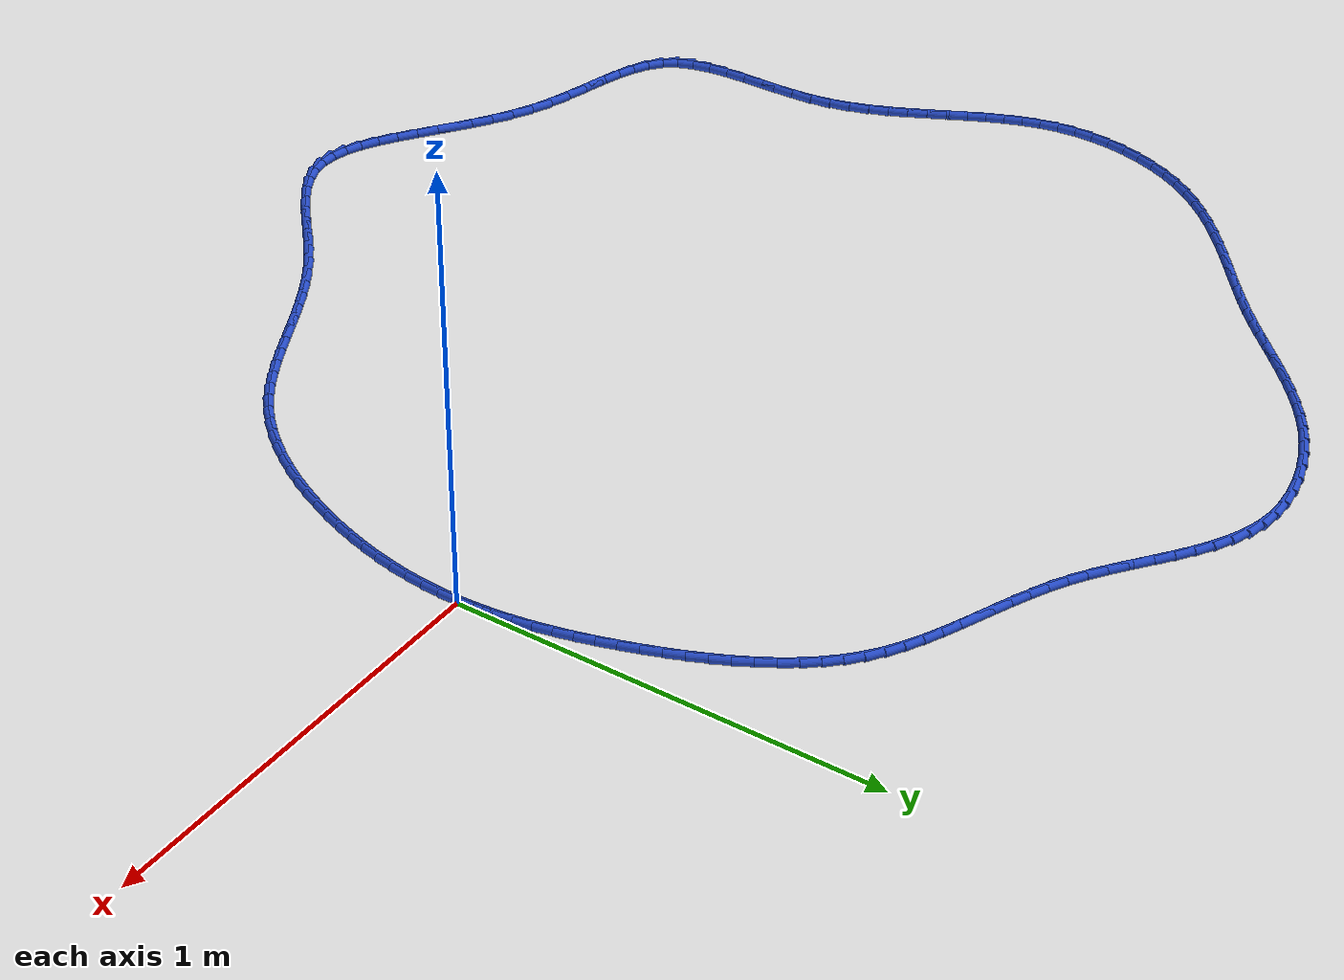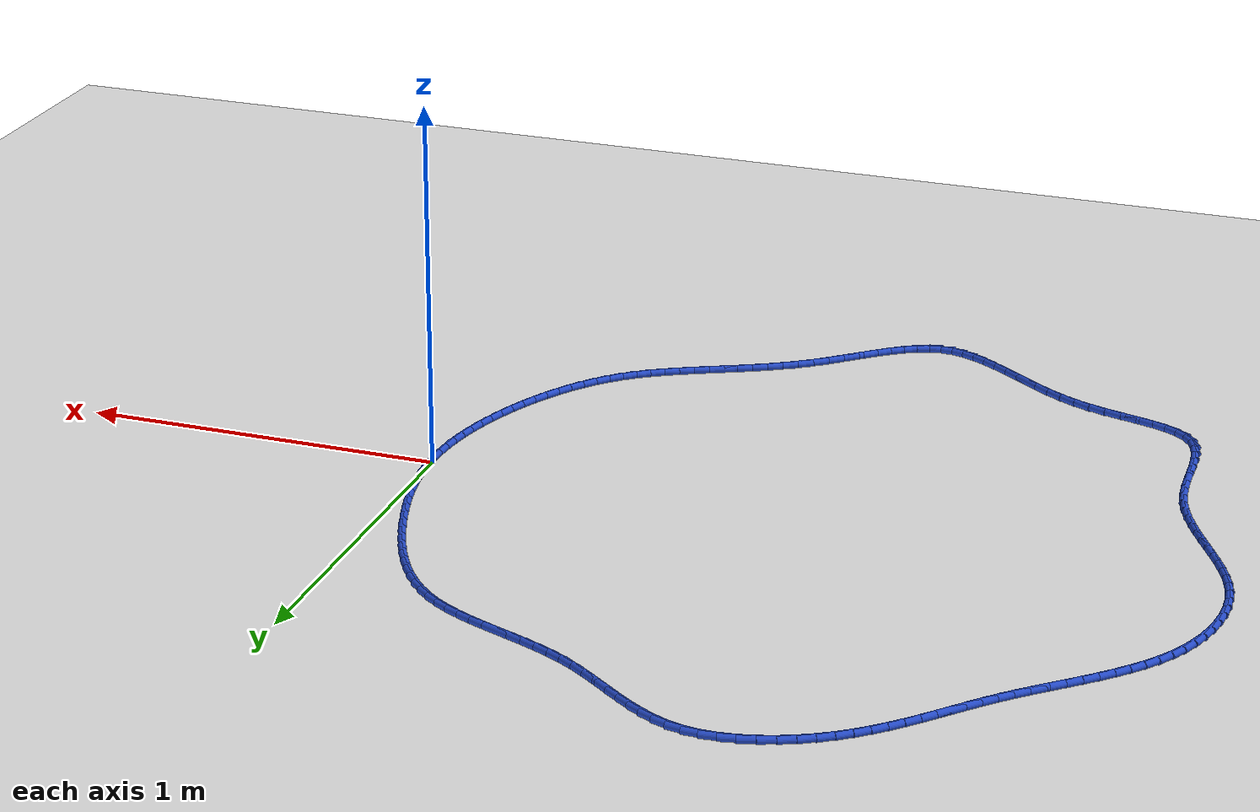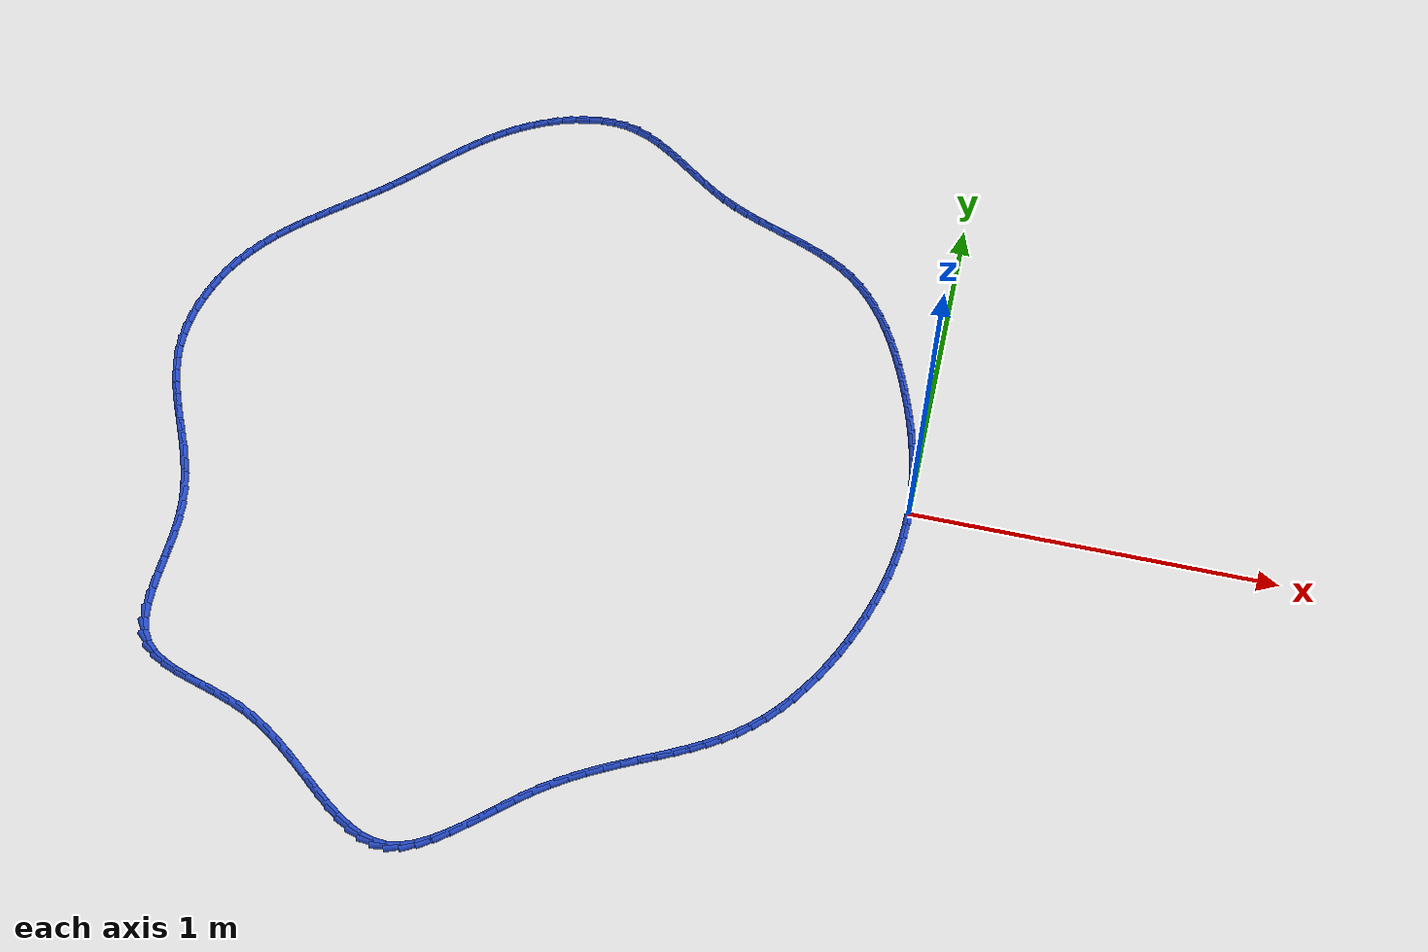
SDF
<sdf version="1.6">
 <world name="default">
  <light name="sun" type="directional">
   <pose>0 0 10 0 -0 0</pose>
   <diffuse>0.8 0.8 0.8 1</diffuse>
   <specular>0.2 0.2 0.2 1</specular>
   <attenuation>
    <range>1000</range>
    <constant>0.9</constant>
    <linear>0.01</linear>
    <quadratic>0.001</quadratic>
   </attenuation>
   <direction>-0.5 0.1 -0.9</direction>
  </light>
  <model name="ground_plane">
   <static>1</static>
   <link name="link">
    <collision name="collision">
     <geometry><plane><normal>0 0 1</normal><size>100 100</size></plane></geometry>
     <surface><friction><ode><mu>100</mu><mu2>50</mu2></ode></friction></surface>
    </collision>
    <visual name="visual">
     <cast_shadows>0</cast_shadows>
     <geometry><plane><normal>0 0 1</normal><size>100 100</size></plane></geometry>
     <material>
      <script><uri>file://media/materials/scripts/gazebo.material</uri><name>Gazebo/WhiteGlow</name></script>
     </material>
    </visual>
   </link>
  </model>
  <gravity>0 0 -9.8</gravity>
  <magnetic_field>6e-06 2.3e-05 -4.2e-05</magnetic_field>
  <atmosphere type="adiabatic"/>
  <physics name="default_physics" default="0" type="ode">
   <max_step_size>0.001</max_step_size>
   <real_time_factor>1</real_time_factor>
   <real_time_update_rate>1000</real_time_update_rate>
  </physics>
  <scene><ambient>0.4 0.4 0.4 1</ambient><background>0.7 0.7 0.7 1</background><shadows>1</shadows></scene>
  <spherical_coordinates>
   <surface_model>EARTH_WGS84</surface_model>
   <latitude_deg>0</latitude_deg>
   <longitude_deg>0</longitude_deg>
   <elevation>0</elevation>
   <heading_deg>0</heading_deg>
  </spherical_coordinates>
  <model name="line">
   <link name="link_0">
    <pose>1.734723475976807e-17 -6.938893903907228e-17 0.01 0 1.57 -1.537088208217915</pose>
    <collision name="collision">
     <geometry><cylinder><radius>0.01</radius><length>0.08</length></cylinder></geometry>
    </collision>
    <visual name="visual">
     <material>
      <script><name>Gazebo/Blue</name><uri>file://media/materials/scripts/gazebo.material</uri></script>
     </material>
     <geometry><cylinder><radius>0.01</radius><length>0.08</length></cylinder></geometry>
    </visual>
   </link>
   <link name="link_1">
    <pose>-0.0014326370155766216 0.04248514689465583 0.01 0 1.57 -1.4900448950670233</pose>
    <collision name="collision">
     <geometry><cylinder><radius>0.01</radius><length>0.08</length></cylinder></geometry>
    </collision>
    <visual name="visual">
     <material>
      <script><name>Gazebo/Blue</name><uri>file://media/materials/scripts/gazebo.material</uri></script>
     </material>
     <geometry><cylinder><radius>0.01</radius><length>0.08</length></cylinder></geometry>
    </visual>
   </link>
   <link name="link_2">
    <pose>-0.004863285648381987 0.08487682299513721 0.01 0 1.57 -1.4458391523767355</pose>
    <collision name="collision">
     <geometry><cylinder><radius>0.01</radius><length>0.08</length></cylinder></geometry>
    </collision>
    <visual name="visual">
     <material>
      <script><name>Gazebo/Blue</name><uri>file://media/materials/scripts/gazebo.material</uri></script>
     </material>
     <geometry><cylinder><radius>0.01</radius><length>0.08</length></cylinder></geometry>
    </visual>
   </link>
   <link name="link_3">
    <pose>-0.010178372033244888 0.1271904699988892 0.01 0 1.57 -1.4046321092932093</pose>
    <collision name="collision">
     <geometry><cylinder><radius>0.01</radius><length>0.08</length></cylinder></geometry>
    </collision>
    <visual name="visual">
     <material>
      <script><name>Gazebo/Blue</name><uri>file://media/materials/scripts/gazebo.material</uri></script>
     </material>
     <geometry><cylinder><radius>0.01</radius><length>0.08</length></cylinder></geometry>
    </visual>
   </link>
   <link name="link_4">
    <pose>-0.01726432230499409 0.1694415296033568 0.01 0 1.57 -1.3665194220279926</pose>
    <collision name="collision">
     <geometry><cylinder><radius>0.01</radius><length>0.08</length></cylinder></geometry>
    </collision>
    <visual name="visual">
     <material>
      <script><name>Gazebo/Blue</name><uri>file://media/materials/scripts/gazebo.material</uri></script>
     </material>
     <geometry><cylinder><radius>0.01</radius><length>0.08</length></cylinder></geometry>
    </visual>
   </link>
   <link name="link_5">
    <pose>-0.02600756259845842 0.21164544350598505 0.01 0 1.57 -1.3315411912900412</pose>
    <collision name="collision">
     <geometry><cylinder><radius>0.01</radius><length>0.08</length></cylinder></geometry>
    </collision>
    <visual name="visual">
     <material>
      <script><name>Gazebo/Blue</name><uri>file://media/materials/scripts/gazebo.material</uri></script>
     </material>
     <geometry><cylinder><radius>0.01</radius><length>0.08</length></cylinder></geometry>
    </visual>
   </link>
   <link name="link_6">
    <pose>-0.03629451904846665 0.253817653404219 0.01 0 1.57 -1.2996928327638817</pose>
    <collision name="collision">
     <geometry><cylinder><radius>0.01</radius><length>0.08</length></cylinder></geometry>
    </collision>
    <visual name="visual">
     <material>
      <script><name>Gazebo/Blue</name><uri>file://media/materials/scripts/gazebo.material</uri></script>
     </material>
     <geometry><cylinder><radius>0.01</radius><length>0.08</length></cylinder></geometry>
    </visual>
   </link>
   <link name="link_7">
    <pose>-0.0480116177898476 0.2959736009955038 0.01 0 1.57 -1.2709357973583177</pose>
    <collision name="collision">
     <geometry><cylinder><radius>0.01</radius><length>0.08</length></cylinder></geometry>
    </collision>
    <visual name="visual">
     <material>
      <script><name>Gazebo/Blue</name><uri>file://media/materials/scripts/gazebo.material</uri></script>
     </material>
     <geometry><cylinder><radius>0.01</radius><length>0.08</length></cylinder></geometry>
    </visual>
   </link>
   <link name="link_8">
    <pose>-0.061045284957430015 0.3381287279772843 0.01 0 1.57 -1.2452074052400846</pose>
    <collision name="collision">
     <geometry><cylinder><radius>0.01</radius><length>0.08</length></cylinder></geometry>
    </collision>
    <visual name="visual">
     <material>
      <script><name>Gazebo/Blue</name><uri>file://media/materials/scripts/gazebo.material</uri></script>
     </material>
     <geometry><cylinder><radius>0.01</radius><length>0.08</length></cylinder></geometry>
    </visual>
   </link>
   <link name="link_9">
    <pose>-0.07528194668604274 0.38029847604700573 0.01 0 1.57 -1.2213718378517162</pose>
    <collision name="collision">
     <geometry><cylinder><radius>0.01</radius><length>0.08</length></cylinder></geometry>
    </collision>
    <visual name="visual">
     <material>
      <script><name>Gazebo/Blue</name><uri>file://media/materials/scripts/gazebo.material</uri></script>
     </material>
     <geometry><cylinder><radius>0.01</radius><length>0.08</length></cylinder></geometry>
    </visual>
   </link>
   <link name="link_10">
    <pose>-0.09064137325140968 0.42245111007388936 0.01 0 1.57 -1.1942485164224237</pose>
    <collision name="collision">
     <geometry><cylinder><radius>0.01</radius><length>0.08</length></cylinder></geometry>
    </collision>
    <visual name="visual">
     <material>
      <script><name>Gazebo/Blue</name><uri>file://media/materials/scripts/gazebo.material</uri></script>
     </material>
     <geometry><cylinder><radius>0.01</radius><length>0.08</length></cylinder></geometry>
    </visual>
   </link>
   <link name="link_11">
    <pose>-0.10720141545751365 0.4643312353057971 0.01 0 1.57 -1.1619965003583548</pose>
    <collision name="collision">
     <geometry><cylinder><radius>0.01</radius><length>0.08</length></cylinder></geometry>
    </collision>
    <visual name="visual">
     <material>
      <script><name>Gazebo/Blue</name><uri>file://media/materials/scripts/gazebo.material</uri></script>
     </material>
     <geometry><cylinder><radius>0.01</radius><length>0.08</length></cylinder></geometry>
    </visual>
   </link>
   <link name="link_12">
    <pose>-0.12508672304748836 0.5056172436933182 0.01 0 1.57 -1.1241323493664084</pose>
    <collision name="collision">
     <geometry><cylinder><radius>0.01</radius><length>0.08</length></cylinder></geometry>
    </collision>
    <visual name="visual">
     <material>
      <script><name>Gazebo/Blue</name><uri>file://media/materials/scripts/gazebo.material</uri></script>
     </material>
     <geometry><cylinder><radius>0.01</radius><length>0.08</length></cylinder></geometry>
    </visual>
   </link>
   <link name="link_13">
    <pose>-0.14442195294032106 0.545987517034314 0.01 0 1.57 -1.0800650414751405</pose>
    <collision name="collision">
     <geometry><cylinder><radius>0.01</radius><length>0.08</length></cylinder></geometry>
    </collision>
    <visual name="visual">
     <material>
      <script><name>Gazebo/Blue</name><uri>file://media/materials/scripts/gazebo.material</uri></script>
     </material>
     <geometry><cylinder><radius>0.01</radius><length>0.08</length></cylinder></geometry>
    </visual>
   </link>
   <link name="link_14">
    <pose>-0.16533176205499883 0.5851204371266457 0.01 0 1.57 -1.0291121252035573</pose>
    <collision name="collision">
     <geometry><cylinder><radius>0.01</radius><length>0.08</length></cylinder></geometry>
    </collision>
    <visual name="visual">
     <material>
      <script><name>Gazebo/Blue</name><uri>file://media/materials/scripts/gazebo.material</uri></script>
     </material>
     <geometry><cylinder><radius>0.01</radius><length>0.08</length></cylinder></geometry>
    </visual>
   </link>
   <link name="link_15">
    <pose>-0.18794080731050894 0.6226943857681746 0.01 0 1.57 -0.9705330578535908</pose>
    <collision name="collision">
     <geometry><cylinder><radius>0.01</radius><length>0.08</length></cylinder></geometry>
    </collision>
    <visual name="visual">
     <material>
      <script><name>Gazebo/Blue</name><uri>file://media/materials/scripts/gazebo.material</uri></script>
     </material>
     <geometry><cylinder><radius>0.01</radius><length>0.08</length></cylinder></geometry>
    </visual>
   </link>
   <link name="link_16">
    <pose>-0.21237374562583852 0.6583877447567617 0.01 0 1.57 -0.9035911426681943</pose>
    <collision name="collision">
     <geometry><cylinder><radius>0.01</radius><length>0.08</length></cylinder></geometry>
    </collision>
    <visual name="visual">
     <material>
      <script><name>Gazebo/Blue</name><uri>file://media/materials/scripts/gazebo.material</uri></script>
     </material>
     <geometry><cylinder><radius>0.01</radius><length>0.08</length></cylinder></geometry>
    </visual>
   </link>
   <link name="link_17">
    <pose>-0.2387552339199747 0.6918788958902685 0.01 0 1.57 -0.8276574802019446</pose>
    <collision name="collision">
     <geometry><cylinder><radius>0.01</radius><length>0.08</length></cylinder></geometry>
    </collision>
    <visual name="visual">
     <material>
      <script><name>Gazebo/Blue</name><uri>file://media/materials/scripts/gazebo.material</uri></script>
     </material>
     <geometry><cylinder><radius>0.01</radius><length>0.08</length></cylinder></geometry>
    </visual>
   </link>
   <link name="link_18">
    <pose>-0.26720992911190455 0.7228462209665557 0.01 0 1.57 -0.7423672808591342</pose>
    <collision name="collision">
     <geometry><cylinder><radius>0.01</radius><length>0.08</length></cylinder></geometry>
    </collision>
    <visual name="visual">
     <material>
      <script><name>Gazebo/Blue</name><uri>file://media/materials/scripts/gazebo.material</uri></script>
     </material>
     <geometry><cylinder><radius>0.01</radius><length>0.08</length></cylinder></geometry>
    </visual>
   </link>
   <link name="link_19">
    <pose>-0.29786248812061555 0.7509681017834853 0.01 0 1.57 -0.6488356298176874</pose>
    <collision name="collision">
     <geometry><cylinder><radius>0.01</radius><length>0.08</length></cylinder></geometry>
    </collision>
    <visual name="visual">
     <material>
      <script><name>Gazebo/Blue</name><uri>file://media/materials/scripts/gazebo.material</uri></script>
     </material>
     <geometry><cylinder><radius>0.01</radius><length>0.08</length></cylinder></geometry>
    </visual>
   </link>
   <link name="link_20">
    <pose>-0.33081787241467375 0.7759604354074059 0.01 0 1.57 -0.5612017702716076</pose>
    <collision name="collision">
     <geometry><cylinder><radius>0.01</radius><length>0.08</length></cylinder></geometry>
    </collision>
    <visual name="visual">
     <material>
      <script><name>Gazebo/Blue</name><uri>file://media/materials/scripts/gazebo.material</uri></script>
     </material>
     <geometry><cylinder><radius>0.01</radius><length>0.08</length></cylinder></geometry>
    </visual>
   </link>
   <link name="link_21">
    <pose>-0.3659238832648375 0.7980289494827505 0.01 0 1.57 -0.4899811874783341</pose>
    <collision name="collision">
     <geometry><cylinder><radius>0.01</radius><length>0.08</length></cylinder></geometry>
    </collision>
    <visual name="visual">
     <material>
      <script><name>Gazebo/Blue</name><uri>file://media/materials/scripts/gazebo.material</uri></script>
     </material>
     <geometry><cylinder><radius>0.01</radius><length>0.08</length></cylinder></geometry>
    </visual>
   </link>
   <link name="link_22">
    <pose>-0.40284795887862057 0.8177229214889843 0.01 0 1.57 -0.43562341742948246</pose>
    <collision name="collision">
     <geometry><cylinder><radius>0.01</radius><length>0.08</length></cylinder></geometry>
    </collision>
    <visual name="visual">
     <material>
      <script><name>Gazebo/Blue</name><uri>file://media/materials/scripts/gazebo.material</uri></script>
     </material>
     <geometry><cylinder><radius>0.01</radius><length>0.08</length></cylinder></geometry>
    </visual>
   </link>
   <link name="link_23">
    <pose>-0.4412538098761629 0.8355987290956232 0.01 0 1.57 -0.3976808472469449</pose>
    <collision name="collision">
     <geometry><cylinder><radius>0.01</radius><length>0.08</length></cylinder></geometry>
    </collision>
    <visual name="visual">
     <material>
      <script><name>Gazebo/Blue</name><uri>file://media/materials/scripts/gazebo.material</uri></script>
     </material>
     <geometry><cylinder><radius>0.01</radius><length>0.08</length></cylinder></geometry>
    </visual>
   </link>
   <link name="link_24">
    <pose>-0.48080514687760456 0.8522127499721841 0.01 0 1.57 -0.37546400602719515</pose>
    <collision name="collision">
     <geometry><cylinder><radius>0.01</radius><length>0.08</length></cylinder></geometry>
    </collision>
    <visual name="visual">
     <material>
      <script><name>Gazebo/Blue</name><uri>file://media/materials/scripts/gazebo.material</uri></script>
     </material>
     <geometry><cylinder><radius>0.01</radius><length>0.08</length></cylinder></geometry>
    </visual>
   </link>
   <link name="link_25">
    <pose>-0.5211656805030855 0.8681213617881839 0.01 0 1.57 -0.36833410776010544</pose>
    <collision name="collision">
     <geometry><cylinder><radius>0.01</radius><length>0.08</length></cylinder></geometry>
    </collision>
    <visual name="visual">
     <material>
      <script><name>Gazebo/Blue</name><uri>file://media/materials/scripts/gazebo.material</uri></script>
     </material>
     <geometry><cylinder><radius>0.01</radius><length>0.08</length></cylinder></geometry>
    </visual>
   </link>
   <link name="link_26">
    <pose>-0.5619991213727461 0.8838809422131386 0.01 0 1.57 -0.37584554307478846</pose>
    <collision name="collision">
     <geometry><cylinder><radius>0.01</radius><length>0.08</length></cylinder></geometry>
    </collision>
    <visual name="visual">
     <material>
      <script><name>Gazebo/Blue</name><uri>file://media/materials/scripts/gazebo.material</uri></script>
     </material>
     <geometry><cylinder><radius>0.01</radius><length>0.08</length></cylinder></geometry>
    </visual>
   </link>
   <link name="link_27">
    <pose>-0.6029691801067263 0.9000478689165652 0.01 0 1.57 -0.3977757655474436</pose>
    <collision name="collision">
     <geometry><cylinder><radius>0.01</radius><length>0.08</length></cylinder></geometry>
    </collision>
    <visual name="visual">
     <material>
      <script><name>Gazebo/Blue</name><uri>file://media/materials/scripts/gazebo.material</uri></script>
     </material>
     <geometry><cylinder><radius>0.01</radius><length>0.08</length></cylinder></geometry>
    </visual>
   </link>
   <link name="link_28">
    <pose>-0.6437395673251659 0.9171785195679796 0.01 0 1.57 -0.43406651591498496</pose>
    <collision name="collision">
     <geometry><cylinder><radius>0.01</radius><length>0.08</length></cylinder></geometry>
    </collision>
    <visual name="visual">
     <material>
      <script><name>Gazebo/Blue</name><uri>file://media/materials/scripts/gazebo.material</uri></script>
     </material>
     <geometry><cylinder><radius>0.01</radius><length>0.08</length></cylinder></geometry>
    </visual>
   </link>
   <link name="link_29">
    <pose>-0.6839739936482054 0.9358292718368992 0.01 0 1.57 -0.48468275375835856</pose>
    <collision name="collision">
     <geometry><cylinder><radius>0.01</radius><length>0.08</length></cylinder></geometry>
    </collision>
    <visual name="visual">
     <material>
      <script><name>Gazebo/Blue</name><uri>file://media/materials/scripts/gazebo.material</uri></script>
     </material>
     <geometry><cylinder><radius>0.01</radius><length>0.08</length></cylinder></geometry>
    </visual>
   </link>
   <link name="link_30">
    <pose>-0.7233361696959841 0.9565565033928393 0.01 0 1.57 -0.5469721512562417</pose>
    <collision name="collision">
     <geometry><cylinder><radius>0.01</radius><length>0.08</length></cylinder></geometry>
    </collision>
    <visual name="visual">
     <material>
      <script><name>Gazebo/Blue</name><uri>file://media/materials/scripts/gazebo.material</uri></script>
     </material>
     <geometry><cylinder><radius>0.01</radius><length>0.08</length></cylinder></geometry>
    </visual>
   </link>
   <link name="link_31">
    <pose>-0.7615343112370307 0.9798171436128819 0.01 0 1.57 -0.5996325471452599</pose>
    <collision name="collision">
     <geometry><cylinder><radius>0.01</radius><length>0.08</length></cylinder></geometry>
    </collision>
    <visual name="visual">
     <material>
      <script><name>Gazebo/Blue</name><uri>file://media/materials/scripts/gazebo.material</uri></script>
     </material>
     <geometry><cylinder><radius>0.01</radius><length>0.08</length></cylinder></geometry>
    </visual>
   </link>
   <link name="link_32">
    <pose>-0.7986652449576362 1.0051997573456564 0.01 0 1.57 -0.6323907942733379</pose>
    <collision name="collision">
     <geometry><cylinder><radius>0.01</radius><length>0.08</length></cylinder></geometry>
    </collision>
    <visual name="visual">
     <material>
      <script><name>Gazebo/Blue</name><uri>file://media/materials/scripts/gazebo.material</uri></script>
     </material>
     <geometry><cylinder><radius>0.01</radius><length>0.08</length></cylinder></geometry>
    </visual>
   </link>
   <link name="link_33">
    <pose>-0.8350264224678011 1.0318446061129714 0.01 0 1.57 -0.6457387281941427</pose>
    <collision name="collision">
     <geometry><cylinder><radius>0.01</radius><length>0.08</length></cylinder></geometry>
    </collision>
    <visual name="visual">
     <material>
      <script><name>Gazebo/Blue</name><uri>file://media/materials/scripts/gazebo.material</uri></script>
     </material>
     <geometry><cylinder><radius>0.01</radius><length>0.08</length></cylinder></geometry>
    </visual>
   </link>
   <link name="link_34">
    <pose>-0.870916969366035 1.0588882108514495 0.01 0 1.57 -0.639720575900705</pose>
    <collision name="collision">
     <geometry><cylinder><radius>0.01</radius><length>0.08</length></cylinder></geometry>
    </collision>
    <visual name="visual">
     <material>
      <script><name>Gazebo/Blue</name><uri>file://media/materials/scripts/gazebo.material</uri></script>
     </material>
     <geometry><cylinder><radius>0.01</radius><length>0.08</length></cylinder></geometry>
    </visual>
   </link>
   <link name="link_35">
    <pose>-0.9066360112508475 1.0854670924977126 0.01 0 1.57 -0.6136782997817464</pose>
    <collision name="collision">
     <geometry><cylinder><radius>0.01</radius><length>0.08</length></cylinder></geometry>
    </collision>
    <visual name="visual">
     <material>
      <script><name>Gazebo/Blue</name><uri>file://media/materials/scripts/gazebo.material</uri></script>
     </material>
     <geometry><cylinder><radius>0.01</radius><length>0.08</length></cylinder></geometry>
    </visual>
   </link>
   <link name="link_36">
    <pose>-0.9424826737207479 1.110717771988383 0.01 0 1.57 -0.5662565731893778</pose>
    <collision name="collision">
     <geometry><cylinder><radius>0.01</radius><length>0.08</length></cylinder></geometry>
    </collision>
    <visual name="visual">
     <material>
      <script><name>Gazebo/Blue</name><uri>file://media/materials/scripts/gazebo.material</uri></script>
     </material>
     <geometry><cylinder><radius>0.01</radius><length>0.08</length></cylinder></geometry>
    </visual>
   </link>
   <link name="link_37">
    <pose>-0.9787560823742463 1.1337767702600832 0.01 0 1.57 -0.49564008075611804</pose>
    <collision name="collision">
     <geometry><cylinder><radius>0.01</radius><length>0.08</length></cylinder></geometry>
    </collision>
    <visual name="visual">
     <material>
      <script><name>Gazebo/Blue</name><uri>file://media/materials/scripts/gazebo.material</uri></script>
     </material>
     <geometry><cylinder><radius>0.01</radius><length>0.08</length></cylinder></geometry>
    </visual>
   </link>
   <link name="link_38">
    <pose>-1.0157553628098521 1.1537806082494357 0.01 0 1.57 -0.4001961369150769</pose>
    <collision name="collision">
     <geometry><cylinder><radius>0.01</radius><length>0.08</length></cylinder></geometry>
    </collision>
    <visual name="visual">
     <material>
      <script><name>Gazebo/Blue</name><uri>file://media/materials/scripts/gazebo.material</uri></script>
     </material>
     <geometry><cylinder><radius>0.01</radius><length>0.08</length></cylinder></geometry>
    </visual>
   </link>
   <link name="link_39">
    <pose>-1.0537796406260744 1.1698658068930623 0.01 0 1.57 -0.27972481229337687</pose>
    <collision name="collision">
     <geometry><cylinder><radius>0.01</radius><length>0.08</length></cylinder></geometry>
    </collision>
    <visual name="visual">
     <material>
      <script><name>Gazebo/Blue</name><uri>file://media/materials/scripts/gazebo.material</uri></script>
     </material>
     <geometry><cylinder><radius>0.01</radius><length>0.08</length></cylinder></geometry>
    </visual>
   </link>
   <link name="link_40">
    <pose>-1.0931280414214237 1.1811688871275863 0.01 0 1.57 -0.1390623356590259</pose>
    <collision name="collision">
     <geometry><cylinder><radius>0.01</radius><length>0.08</length></cylinder></geometry>
    </collision>
    <visual name="visual">
     <material>
      <script><name>Gazebo/Blue</name><uri>file://media/materials/scripts/gazebo.material</uri></script>
     </material>
     <geometry><cylinder><radius>0.01</radius><length>0.08</length></cylinder></geometry>
    </visual>
   </link>
   <link name="link_41">
    <pose>-1.1340541426265514 1.186897138990622 0.01 0 1.57 -0.0035594008422905163</pose>
    <collision name="collision">
     <geometry><cylinder><radius>0.01</radius><length>0.08</length></cylinder></geometry>
    </collision>
    <visual name="visual">
     <material>
      <script><name>Gazebo/Blue</name><uri>file://media/materials/scripts/gazebo.material</uri></script>
     </material>
     <geometry><cylinder><radius>0.01</radius><length>0.08</length></cylinder></geometry>
    </visual>
   </link>
   <link name="link_42">
    <pose>-1.176303277783253 1.1870475212329663 0.01 0 1.57 0.11429929936295045</pose>
    <collision name="collision">
     <geometry><cylinder><radius>0.01</radius><length>0.08</length></cylinder></geometry>
    </collision>
    <visual name="visual">
     <material>
      <script><name>Gazebo/Blue</name><uri>file://media/materials/scripts/gazebo.material</uri></script>
     </material>
     <geometry><cylinder><radius>0.01</radius><length>0.08</length></cylinder></geometry>
    </visual>
   </link>
   <link name="link_43">
    <pose>-1.2193026989298357 1.182111202210398 0.01 0 1.57 0.2171338606109823</pose>
    <collision name="collision">
     <geometry><cylinder><radius>0.01</radius><length>0.08</length></cylinder></geometry>
    </collision>
    <visual name="visual">
     <material>
      <script><name>Gazebo/Blue</name><uri>file://media/materials/scripts/gazebo.material</uri></script>
     </material>
     <geometry><cylinder><radius>0.01</radius><length>0.08</length></cylinder></geometry>
    </visual>
   </link>
   <link name="link_44">
    <pose>-1.26247478088094 1.1725869281188246 0.01 0 1.57 0.30817515680366264</pose>
    <collision name="collision">
     <geometry><cylinder><radius>0.01</radius><length>0.08</length></cylinder></geometry>
    </collision>
    <visual name="visual">
     <material>
      <script><name>Gazebo/Blue</name><uri>file://media/materials/scripts/gazebo.material</uri></script>
     </material>
     <geometry><cylinder><radius>0.01</radius><length>0.08</length></cylinder></geometry>
    </visual>
   </link>
   <link name="link_45">
    <pose>-1.3052418984512053 1.158973445154156 0.01 0 1.57 0.39057740820643516</pose>
    <collision name="collision">
     <geometry><cylinder><radius>0.01</radius><length>0.08</length></cylinder></geometry>
    </collision>
    <visual name="visual">
     <material>
      <script><name>Gazebo/Blue</name><uri>file://media/materials/scripts/gazebo.material</uri></script>
     </material>
     <geometry><cylinder><radius>0.01</radius><length>0.08</length></cylinder></geometry>
    </visual>
   </link>
   <link name="link_46">
    <pose>-1.347026426455272 1.1417694995122998 0.01 0 1.57 0.46729058842114163</pose>
    <collision name="collision">
     <geometry><cylinder><radius>0.01</radius><length>0.08</length></cylinder></geometry>
    </collision>
    <visual name="visual">
     <material>
      <script><name>Gazebo/Blue</name><uri>file://media/materials/scripts/gazebo.material</uri></script>
     </material>
     <geometry><cylinder><radius>0.01</radius><length>0.08</length></cylinder></geometry>
    </visual>
   </link>
   <link name="link_47">
    <pose>-1.38725073970778 1.1214738373891653 0.01 0 1.57 0.5410305204586531</pose>
    <collision name="collision">
     <geometry><cylinder><radius>0.01</radius><length>0.08</length></cylinder></geometry>
    </collision>
    <visual name="visual">
     <material>
      <script><name>Gazebo/Blue</name><uri>file://media/materials/scripts/gazebo.material</uri></script>
     </material>
     <geometry><cylinder><radius>0.01</radius><length>0.08</length></cylinder></geometry>
    </visual>
   </link>
   <link name="link_48">
    <pose>-1.4253504681780664 1.0985823282952816 0.01 0 1.57 0.6108868005704579</pose>
    <collision name="collision">
     <geometry><cylinder><radius>0.01</radius><length>0.08</length></cylinder></geometry>
    </collision>
    <visual name="visual">
     <material>
      <script><name>Gazebo/Blue</name><uri>file://media/materials/scripts/gazebo.material</uri></script>
     </material>
     <geometry><cylinder><radius>0.01</radius><length>0.08</length></cylinder></geometry>
    </visual>
   </link>
   <link name="link_49">
    <pose>-1.4611657360647023 1.073503056825669 0.01 0 1.57 0.6727331271956344</pose>
    <collision name="collision">
     <geometry><cylinder><radius>0.01</radius><length>0.08</length></cylinder></geometry>
    </collision>
    <visual name="visual">
     <material>
      <script><name>Gazebo/Blue</name><uri>file://media/materials/scripts/gazebo.material</uri></script>
     </material>
     <geometry><cylinder><radius>0.01</radius><length>0.08</length></cylinder></geometry>
    </visual>
   </link>
   <link name="link_50">
    <pose>-1.495005733812268 1.0465423089888706 0.01 0 1.57 0.7252398496523266</pose>
    <collision name="collision">
     <geometry><cylinder><radius>0.01</radius><length>0.08</length></cylinder></geometry>
    </collision>
    <visual name="visual">
     <material>
      <script><name>Gazebo/Blue</name><uri>file://media/materials/scripts/gazebo.material</uri></script>
     </material>
     <geometry><cylinder><radius>0.01</radius><length>0.08</length></cylinder></geometry>
    </visual>
   </link>
   <link name="link_51">
    <pose>-1.5272059102918196 1.018000672087283 0.01 0 1.57 0.767713819048618</pose>
    <collision name="collision">
     <geometry><cylinder><radius>0.01</radius><length>0.08</length></cylinder></geometry>
    </collision>
    <visual name="visual">
     <material>
      <script><name>Gazebo/Blue</name><uri>file://media/materials/scripts/gazebo.material</uri></script>
     </material>
     <geometry><cylinder><radius>0.01</radius><length>0.08</length></cylinder></geometry>
    </visual>
   </link>
   <link name="link_52">
    <pose>-1.5581017143744162 0.9881787334233055 0.01 0 1.57 0.7998018056155519</pose>
    <collision name="collision">
     <geometry><cylinder><radius>0.01</radius><length>0.08</length></cylinder></geometry>
    </collision>
    <visual name="visual">
     <material>
      <script><name>Gazebo/Blue</name><uri>file://media/materials/scripts/gazebo.material</uri></script>
     </material>
     <geometry><cylinder><radius>0.01</radius><length>0.08</length></cylinder></geometry>
    </visual>
   </link>
   <link name="link_53">
    <pose>-1.5880285949311141 0.9573770802993341 0.01 0 1.57 0.8213744673745932</pose>
    <collision name="collision">
     <geometry><cylinder><radius>0.01</radius><length>0.08</length></cylinder></geometry>
    </collision>
    <visual name="visual">
     <material>
      <script><name>Gazebo/Blue</name><uri>file://media/materials/scripts/gazebo.material</uri></script>
     </material>
     <geometry><cylinder><radius>0.01</radius><length>0.08</length></cylinder></geometry>
    </visual>
   </link>
   <link name="link_54">
    <pose>-1.6173220008329716 0.9258963000177679 0.01 0 1.57 0.8324254009968024</pose>
    <collision name="collision">
     <geometry><cylinder><radius>0.01</radius><length>0.08</length></cylinder></geometry>
    </collision>
    <visual name="visual">
     <material>
      <script><name>Gazebo/Blue</name><uri>file://media/materials/scripts/gazebo.material</uri></script>
     </material>
     <geometry><cylinder><radius>0.01</radius><length>0.08</length></cylinder></geometry>
    </visual>
   </link>
   <link name="link_55">
    <pose>-1.6463173809510463 0.894036979881004 0.01 0 1.57 0.8329997999224895</pose>
    <collision name="collision">
     <geometry><cylinder><radius>0.01</radius><length>0.08</length></cylinder></geometry>
    </collision>
    <visual name="visual">
     <material>
      <script><name>Gazebo/Blue</name><uri>file://media/materials/scripts/gazebo.material</uri></script>
     </material>
     <geometry><cylinder><radius>0.01</radius><length>0.08</length></cylinder></geometry>
    </visual>
   </link>
   <link name="link_56">
    <pose>-1.6753501841563954 0.8620997071914395 0.01 0 1.57 0.8231575465556834</pose>
    <collision name="collision">
     <geometry><cylinder><radius>0.01</radius><length>0.08</length></cylinder></geometry>
    </collision>
    <visual name="visual">
     <material>
      <script><name>Gazebo/Blue</name><uri>file://media/materials/scripts/gazebo.material</uri></script>
     </material>
     <geometry><cylinder><radius>0.01</radius><length>0.08</length></cylinder></geometry>
    </visual>
   </link>
   <link name="link_57">
    <pose>-1.7047558593200762 0.8303850692514729 0.01 0 1.57 0.8029709837357847</pose>
    <collision name="collision">
     <geometry><cylinder><radius>0.01</radius><length>0.08</length></cylinder></geometry>
    </collision>
    <visual name="visual">
     <material>
      <script><name>Gazebo/Blue</name><uri>file://media/materials/scripts/gazebo.material</uri></script>
     </material>
     <geometry><cylinder><radius>0.01</radius><length>0.08</length></cylinder></geometry>
    </visual>
   </link>
   <link name="link_58">
    <pose>-1.7348698553131479 0.7991936533635018 0.01 0 1.57 0.7737922068224099</pose>
    <collision name="collision">
     <geometry><cylinder><radius>0.01</radius><length>0.08</length></cylinder></geometry>
    </collision>
    <visual name="visual">
     <material>
      <script><name>Gazebo/Blue</name><uri>file://media/materials/scripts/gazebo.material</uri></script>
     </material>
     <geometry><cylinder><radius>0.01</radius><length>0.08</length></cylinder></geometry>
    </visual>
   </link>
   <link name="link_59">
    <pose>-1.7659859614970173 0.7687915568278687 0.01 0 1.57 0.7478658680084495</pose>
    <collision name="collision">
     <geometry><cylinder><radius>0.01</radius><length>0.08</length></cylinder></geometry>
    </collision>
    <visual name="visual">
     <material>
      <script><name>Gazebo/Blue</name><uri>file://media/materials/scripts/gazebo.material</uri></script>
     </material>
     <geometry><cylinder><radius>0.01</radius><length>0.08</length></cylinder></geometry>
    </visual>
   </link>
   <link name="link_60">
    <pose>-1.7979882410826868 0.7391056637403282 0.01 0 1.57 0.7319609711398238</pose>
    <collision name="collision">
     <geometry><cylinder><radius>0.01</radius><length>0.08</length></cylinder></geometry>
    </collision>
    <visual name="visual">
     <material>
      <script><name>Gazebo/Blue</name><uri>file://media/materials/scripts/gazebo.material</uri></script>
     </material>
     <geometry><cylinder><radius>0.01</radius><length>0.08</length></cylinder></geometry>
    </visual>
   </link>
   <link name="link_61">
    <pose>-1.8305279941316612 0.709870153059869 0.01 0 1.57 0.7260193806174606</pose>
    <collision name="collision">
     <geometry><cylinder><radius>0.01</radius><length>0.08</length></cylinder></geometry>
    </collision>
    <visual name="visual">
     <material>
      <script><name>Gazebo/Blue</name><uri>file://media/materials/scripts/gazebo.material</uri></script>
     </material>
     <geometry><cylinder><radius>0.01</radius><length>0.08</length></cylinder></geometry>
    </visual>
   </link>
   <link name="link_62">
    <pose>-1.8632538416149276 0.6808169857203956 0.01 0 1.57 0.7299973493644972</pose>
    <collision name="collision">
     <geometry><cylinder><radius>0.01</radius><length>0.08</length></cylinder></geometry>
    </collision>
    <visual name="visual">
     <material>
      <script><name>Gazebo/Blue</name><uri>file://media/materials/scripts/gazebo.material</uri></script>
     </material>
     <geometry><cylinder><radius>0.01</radius><length>0.08</length></cylinder></geometry>
    </visual>
   </link>
   <link name="link_63">
    <pose>-1.8958144045034742 0.6516781226558107 0.01 0 1.57 0.7439619231393854</pose>
    <collision name="collision">
     <geometry><cylinder><radius>0.01</radius><length>0.08</length></cylinder></geometry>
    </collision>
    <visual name="visual">
     <material>
      <script><name>Gazebo/Blue</name><uri>file://media/materials/scripts/gazebo.material</uri></script>
     </material>
     <geometry><cylinder><radius>0.01</radius><length>0.08</length></cylinder></geometry>
    </visual>
   </link>
   <link name="link_64">
    <pose>-1.927858303768288 0.6221855248000185 0.01 0 1.57 0.768080903906371</pose>
    <collision name="collision">
     <geometry><cylinder><radius>0.01</radius><length>0.08</length></cylinder></geometry>
    </collision>
    <visual name="visual">
     <material>
      <script><name>Gazebo/Blue</name><uri>file://media/materials/scripts/gazebo.material</uri></script>
     </material>
     <geometry><cylinder><radius>0.01</radius><length>0.08</length></cylinder></geometry>
    </visual>
   </link>
   <link name="link_65">
    <pose>-1.9590341603803558 0.5920711530869222 0.01 0 1.57 0.8025837917932958</pose>
    <collision name="collision">
     <geometry><cylinder><radius>0.01</radius><length>0.08</length></cylinder></geometry>
    </collision>
    <visual name="visual">
     <material>
      <script><name>Gazebo/Blue</name><uri>file://media/materials/scripts/gazebo.material</uri></script>
     </material>
     <geometry><cylinder><radius>0.01</radius><length>0.08</length></cylinder></geometry>
    </visual>
   </link>
   <link name="link_66">
    <pose>-1.9889905953106664 0.5610669684504249 0.01 0 1.57 0.8476882049593696</pose>
    <collision name="collision">
     <geometry><cylinder><radius>0.01</radius><length>0.08</length></cylinder></geometry>
    </collision>
    <visual name="visual">
     <material>
      <script><name>Gazebo/Blue</name><uri>file://media/materials/scripts/gazebo.material</uri></script>
     </material>
     <geometry><cylinder><radius>0.01</radius><length>0.08</length></cylinder></geometry>
    </visual>
   </link>
   <link name="link_67">
    <pose>-2.017376229530206 0.528904931824431 0.01 0 1.57 0.9034858064429354</pose>
    <collision name="collision">
     <geometry><cylinder><radius>0.01</radius><length>0.08</length></cylinder></geometry>
    </collision>
    <visual name="visual">
     <material>
      <script><name>Gazebo/Blue</name><uri>file://media/materials/scripts/gazebo.material</uri></script>
     </material>
     <geometry><cylinder><radius>0.01</radius><length>0.08</length></cylinder></geometry>
    </visual>
   </link>
   <link name="link_68">
    <pose>-2.0438396840099626 0.49531700414284324 0.01 0 1.57 0.9697877017056</pose>
    <collision name="collision">
     <geometry><cylinder><radius>0.01</radius><length>0.08</length></cylinder></geometry>
    </collision>
    <visual name="visual">
     <material>
      <script><name>Gazebo/Blue</name><uri>file://media/materials/scripts/gazebo.material</uri></script>
     </material>
     <geometry><cylinder><radius>0.01</radius><length>0.08</length></cylinder></geometry>
    </visual>
   </link>
   <link name="link_69">
    <pose>-2.0680295797209243 0.46003514633956594 0.01 0 1.57 1.0459454103071812</pose>
    <collision name="collision">
     <geometry><cylinder><radius>0.01</radius><length>0.08</length></cylinder></geometry>
    </collision>
    <visual name="visual">
     <material>
      <script><name>Gazebo/Blue</name><uri>file://media/materials/scripts/gazebo.material</uri></script>
     </material>
     <geometry><cylinder><radius>0.01</radius><length>0.08</length></cylinder></geometry>
    </visual>
   </link>
   <link name="link_70">
    <pose>-2.0895945376340777 0.42279131934850206 0.01 0 1.57 1.1291735530996527</pose>
    <collision name="collision">
     <geometry><cylinder><radius>0.01</radius><length>0.08</length></cylinder></geometry>
    </collision>
    <visual name="visual">
     <material>
      <script><name>Gazebo/Blue</name><uri>file://media/materials/scripts/gazebo.material</uri></script>
     </material>
     <geometry><cylinder><radius>0.01</radius><length>0.08</length></cylinder></geometry>
    </visual>
   </link>
   <link name="link_71">
    <pose>-2.108211925270316 0.3834114835197722 0.01 0 1.57 1.211040522992394</pose>
    <collision name="collision">
     <geometry><cylinder><radius>0.01</radius><length>0.08</length></cylinder></geometry>
    </collision>
    <visual name="visual">
     <material>
      <script><name>Gazebo/Blue</name><uri>file://media/materials/scripts/gazebo.material</uri></script>
     </material>
     <geometry><cylinder><radius>0.01</radius><length>0.08</length></cylinder></geometry>
    </visual>
   </link>
   <link name="link_72">
    <pose>-2.1237086165529653 0.3422104757676396 0.01 0 1.57 1.2904447831189645</pose>
    <collision name="collision">
     <geometry><cylinder><radius>0.01</radius><length>0.08</length></cylinder></geometry>
    </collision>
    <visual name="visual">
     <material>
      <script><name>Gazebo/Blue</name><uri>file://media/materials/scripts/gazebo.material</uri></script>
     </material>
     <geometry><cylinder><radius>0.01</radius><length>0.08</length></cylinder></geometry>
    </visual>
   </link>
   <link name="link_73">
    <pose>-2.135959936318275 0.29966156445449044 0.01 0 1.57 1.369051097048772</pose>
    <collision name="collision">
     <geometry><cylinder><radius>0.01</radius><length>0.08</length></cylinder></geometry>
    </collision>
    <visual name="visual">
     <material>
      <script><name>Gazebo/Blue</name><uri>file://media/materials/scripts/gazebo.material</uri></script>
     </material>
     <geometry><cylinder><radius>0.01</radius><length>0.08</length></cylinder></geometry>
    </visual>
   </link>
   <link name="link_74">
    <pose>-2.14484123439578 0.2562380996691895 0.01 0 1.57 1.448496642157767</pose>
    <collision name="collision">
     <geometry><cylinder><radius>0.01</radius><length>0.08</length></cylinder></geometry>
    </collision>
    <visual name="visual">
     <material>
      <script><name>Gazebo/Blue</name><uri>file://media/materials/scripts/gazebo.material</uri></script>
     </material>
     <geometry><cylinder><radius>0.01</radius><length>0.08</length></cylinder></geometry>
    </visual>
   </link>
   <link name="link_75">
    <pose>-2.1502278606150185 0.2124134315006007 0.01 0 1.57 1.5304250776097263</pose>
    <collision name="collision">
     <geometry><cylinder><radius>0.01</radius><length>0.08</length></cylinder></geometry>
    </collision>
    <visual name="visual">
     <material>
      <script><name>Gazebo/Blue</name><uri>file://media/materials/scripts/gazebo.material</uri></script>
     </material>
     <geometry><cylinder><radius>0.01</radius><length>0.08</length></cylinder></geometry>
    </visual>
   </link>
   <link name="link_76">
    <pose>-2.1519951648055238 0.16866091003758737 0.01 0 1.57 -1.5250794386060509</pose>
    <collision name="collision">
     <geometry><cylinder><radius>0.01</radius><length>0.08</length></cylinder></geometry>
    </collision>
    <visual name="visual">
     <material>
      <script><name>Gazebo/Blue</name><uri>file://media/materials/scripts/gazebo.material</uri></script>
     </material>
     <geometry><cylinder><radius>0.01</radius><length>0.08</length></cylinder></geometry>
    </visual>
   </link>
   <link name="link_77">
    <pose>-2.150018496796834 0.1254538853690147 0.01 0 1.57 -1.4331425958365656</pose>
    <collision name="collision">
     <geometry><cylinder><radius>0.01</radius><length>0.08</length></cylinder></geometry>
    </collision>
    <visual name="visual">
     <material>
      <script><name>Gazebo/Blue</name><uri>file://media/materials/scripts/gazebo.material</uri></script>
     </material>
     <geometry><cylinder><radius>0.01</radius><length>0.08</length></cylinder></geometry>
    </visual>
   </link>
   <link name="link_78">
    <pose>-2.1441740566232745 0.08326484434507236 0.01 0 1.57 -1.339411558170758</pose>
    <collision name="collision">
     <geometry><cylinder><radius>0.01</radius><length>0.08</length></cylinder></geometry>
    </collision>
    <visual name="visual">
     <material>
      <script><name>Gazebo/Blue</name><uri>file://media/materials/scripts/gazebo.material</uri></script>
     </material>
     <geometry><cylinder><radius>0.01</radius><length>0.08</length></cylinder></geometry>
    </visual>
   </link>
   <link name="link_79">
    <pose>-2.1345375615354 0.04236369794381593 0.01 0 1.57 -1.2574487270368455</pose>
    <collision name="collision">
     <geometry><cylinder><radius>0.01</radius><length>0.08</length></cylinder></geometry>
    </collision>
    <visual name="visual">
     <material>
      <script><name>Gazebo/Blue</name><uri>file://media/materials/scripts/gazebo.material</uri></script>
     </material>
     <geometry><cylinder><radius>0.01</radius><length>0.08</length></cylinder></geometry>
    </visual>
   </link>
   <link name="link_80">
    <pose>-2.121639737548715 0.0025583729640198897 0.01 0 1.57 -1.1907538282543098</pose>
    <collision name="collision">
     <geometry><cylinder><radius>0.01</radius><length>0.08</length></cylinder></geometry>
    </collision>
    <visual name="visual">
     <material>
      <script><name>Gazebo/Blue</name><uri>file://media/materials/scripts/gazebo.material</uri></script>
     </material>
     <geometry><cylinder><radius>0.01</radius><length>0.08</length></cylinder></geometry>
    </visual>
   </link>
   <link name="link_81">
    <pose>-2.106074433958102 -0.0364072947728164 0.01 0 1.57 -1.1400203359540626</pose>
    <collision name="collision">
     <geometry><cylinder><radius>0.01</radius><length>0.08</length></cylinder></geometry>
    </collision>
    <visual name="visual">
     <material>
      <script><name>Gazebo/Blue</name><uri>file://media/materials/scripts/gazebo.material</uri></script>
     </material>
     <geometry><cylinder><radius>0.01</radius><length>0.08</length></cylinder></geometry>
    </visual>
   </link>
   <link name="link_82">
    <pose>-2.0884355000584405 -0.07478946944519438 0.01 0 1.57 -1.10523139265718</pose>
    <collision name="collision">
     <geometry><cylinder><radius>0.01</radius><length>0.08</length></cylinder></geometry>
    </collision>
    <visual name="visual">
     <material>
      <script><name>Gazebo/Blue</name><uri>file://media/materials/scripts/gazebo.material</uri></script>
     </material>
     <geometry><cylinder><radius>0.01</radius><length>0.08</length></cylinder></geometry>
    </visual>
   </link>
   <link name="link_83">
    <pose>-2.0693167851446113 -0.11284431523161337 0.01 0 1.57 -1.0860455700476184</pose>
    <collision name="collision">
     <geometry><cylinder><radius>0.01</radius><length>0.08</length></cylinder></geometry>
    </collision>
    <visual name="visual">
     <material>
      <script><name>Gazebo/Blue</name><uri>file://media/materials/scripts/gazebo.material</uri></script>
     </material>
     <geometry><cylinder><radius>0.01</radius><length>0.08</length></cylinder></geometry>
    </visual>
   </link>
   <link name="link_84">
    <pose>-2.049312138511496 -0.1508279963105748 0.01 0 1.57 -1.0820616201482594</pose>
    <collision name="collision">
     <geometry><cylinder><radius>0.01</radius><length>0.08</length></cylinder></geometry>
    </collision>
    <visual name="visual">
     <material>
      <script><name>Gazebo/Blue</name><uri>file://media/materials/scripts/gazebo.material</uri></script>
     </material>
     <geometry><cylinder><radius>0.01</radius><length>0.08</length></cylinder></geometry>
    </visual>
   </link>
   <link name="link_85">
    <pose>-2.0290154094539736 -0.1889966768605793 0.01 0 1.57 -1.092953455381717</pose>
    <collision name="collision">
     <geometry><cylinder><radius>0.01</radius><length>0.08</length></cylinder></geometry>
    </collision>
    <visual name="visual">
     <material>
      <script><name>Gazebo/Blue</name><uri>file://media/materials/scripts/gazebo.material</uri></script>
     </material>
     <geometry><cylinder><radius>0.01</radius><length>0.08</length></cylinder></geometry>
    </visual>
   </link>
   <link name="link_86">
    <pose>-2.009020447266926 -0.2276065210601277 0.01 0 1.57 -1.1184923937611049</pose>
    <collision name="collision">
     <geometry><cylinder><radius>0.01</radius><length>0.08</length></cylinder></geometry>
    </collision>
    <visual name="visual">
     <material>
      <script><name>Gazebo/Blue</name><uri>file://media/materials/scripts/gazebo.material</uri></script>
     </material>
     <geometry><cylinder><radius>0.01</radius><length>0.08</length></cylinder></geometry>
    </visual>
   </link>
   <link name="link_87">
    <pose>-1.9899211012452331 -0.2669136930877213 0.01 0 1.57 -1.1584726141584933</pose>
    <collision name="collision">
     <geometry><cylinder><radius>0.01</radius><length>0.08</length></cylinder></geometry>
    </collision>
    <visual name="visual">
     <material>
      <script><name>Gazebo/Blue</name><uri>file://media/materials/scripts/gazebo.material</uri></script>
     </material>
     <geometry><cylinder><radius>0.01</radius><length>0.08</length></cylinder></geometry>
    </visual>
   </link>
   <link name="link_88">
    <pose>-1.9723112206837752 -0.30717435712185936 0.01 0 1.57 -1.2125501398032072</pose>
    <collision name="collision">
     <geometry><cylinder><radius>0.01</radius><length>0.08</length></cylinder></geometry>
    </collision>
    <visual name="visual">
     <material>
      <script><name>Gazebo/Blue</name><uri>file://media/materials/scripts/gazebo.material</uri></script>
     </material>
     <geometry><cylinder><radius>0.01</radius><length>0.08</length></cylinder></geometry>
    </visual>
   </link>
   <link name="link_89">
    <pose>-1.9567846548774344 -0.34864467734104354 0.01 0 1.57 -1.2800114658058306</pose>
    <collision name="collision">
     <geometry><cylinder><radius>0.01</radius><length>0.08</length></cylinder></geometry>
    </collision>
    <visual name="visual">
     <material>
      <script><name>Gazebo/Blue</name><uri>file://media/materials/scripts/gazebo.material</uri></script>
     </material>
     <geometry><cylinder><radius>0.01</radius><length>0.08</length></cylinder></geometry>
    </visual>
   </link>
   <link name="link_90">
    <pose>-1.9439352531210896 -0.3915808179237743 0.01 0 1.57 -1.3595148100893744</pose>
    <collision name="collision">
     <geometry><cylinder><radius>0.01</radius><length>0.08</length></cylinder></geometry>
    </collision>
    <visual name="visual">
     <material>
      <script><name>Gazebo/Blue</name><uri>file://media/materials/scripts/gazebo.material</uri></script>
     </material>
     <geometry><cylinder><radius>0.01</radius><length>0.08</length></cylinder></geometry>
    </visual>
   </link>
   <link name="link_91">
    <pose>-1.9343568647096223 -0.4362389430485525 0.01 0 1.57 -1.4428558304343264</pose>
    <collision name="collision">
     <geometry><cylinder><radius>0.01</radius><length>0.08</length></cylinder></geometry>
    </collision>
    <visual name="visual">
     <material>
      <script><name>Gazebo/Blue</name><uri>file://media/materials/scripts/gazebo.material</uri></script>
     </material>
     <geometry><cylinder><radius>0.01</radius><length>0.08</length></cylinder></geometry>
    </visual>
   </link>
   <link name="link_92">
    <pose>-1.9283790552215119 -0.48270708679352836 0.01 0 1.57 -1.501618243015796</pose>
    <collision name="collision">
     <geometry><cylinder><radius>0.01</radius><length>0.08</length></cylinder></geometry>
    </collision>
    <visual name="visual">
     <material>
      <script><name>Gazebo/Blue</name><uri>file://media/materials/scripts/gazebo.material</uri></script>
     </material>
     <geometry><cylinder><radius>0.01</radius><length>0.08</length></cylinder></geometry>
    </visual>
   </link>
   <link name="link_93">
    <pose>-1.9250828614265676 -0.5302790032231159 0.01 0 1.57 -1.5309750134360272</pose>
    <collision name="collision">
     <geometry><cylinder><radius>0.01</radius><length>0.08</length></cylinder></geometry>
    </collision>
    <visual name="visual">
     <material>
      <script><name>Gazebo/Blue</name><uri>file://media/materials/scripts/gazebo.material</uri></script>
     </material>
     <geometry><cylinder><radius>0.01</radius><length>0.08</length></cylinder></geometry>
    </visual>
   </link>
   <link name="link_94">
    <pose>-1.9231809810180374 -0.5780141191160821 0.01 0 1.57 -1.5325906902519473</pose>
    <collision name="collision">
     <geometry><cylinder><radius>0.01</radius><length>0.08</length></cylinder></geometry>
    </collision>
    <visual name="visual">
     <material>
      <script><name>Gazebo/Blue</name><uri>file://media/materials/scripts/gazebo.material</uri></script>
     </material>
     <geometry><cylinder><radius>0.01</radius><length>0.08</length></cylinder></geometry>
    </visual>
   </link>
   <link name="link_95">
    <pose>-1.9213860584658315 -0.6249718273919558 0.01 0 1.57 -1.5051229931585943</pose>
    <collision name="collision">
     <geometry><cylinder><radius>0.01</radius><length>0.08</length></cylinder></geometry>
    </collision>
    <visual name="visual">
     <material>
      <script><name>Gazebo/Blue</name><uri>file://media/materials/scripts/gazebo.material</uri></script>
     </material>
     <geometry><cylinder><radius>0.01</radius><length>0.08</length></cylinder></geometry>
    </visual>
   </link>
   <link name="link_96">
    <pose>-1.9184107382398605 -0.6702115209702668 0.01 0 1.57 -1.4436573495802814</pose>
    <collision name="collision">
     <geometry><cylinder><radius>0.01</radius><length>0.08</length></cylinder></geometry>
    </collision>
    <visual name="visual">
     <material>
      <script><name>Gazebo/Blue</name><uri>file://media/materials/scripts/gazebo.material</uri></script>
     </material>
     <geometry><cylinder><radius>0.01</radius><length>0.08</length></cylinder></geometry>
    </visual>
   </link>
   <link name="link_97">
    <pose>-1.9129676648100364 -0.7127925927705431 0.01 0 1.57 -1.3390741584907442</pose>
    <collision name="collision">
     <geometry><cylinder><radius>0.01</radius><length>0.08</length></cylinder></geometry>
    </collision>
    <visual name="visual">
     <material>
      <script><name>Gazebo/Blue</name><uri>file://media/materials/scripts/gazebo.material</uri></script>
     </material>
     <geometry><cylinder><radius>0.01</radius><length>0.08</length></cylinder></geometry>
    </visual>
   </link>
   <link name="link_98">
    <pose>-1.9037694826462683 -0.7517744357123143 0.01 0 1.57 -1.1787343188204447</pose>
    <collision name="collision">
     <geometry><cylinder><radius>0.01</radius><length>0.08</length></cylinder></geometry>
    </collision>
    <visual name="visual">
     <material>
      <script><name>Gazebo/Blue</name><uri>file://media/materials/scripts/gazebo.material</uri></script>
     </material>
     <geometry><cylinder><radius>0.01</radius><length>0.08</length></cylinder></geometry>
    </visual>
   </link>
   <link name="link_99">
    <pose>-1.8895288362184672 -0.7862164427151097 0.01 0 1.57 -0.9534844341967744</pose>
    <collision name="collision">
     <geometry><cylinder><radius>0.01</radius><length>0.08</length></cylinder></geometry>
    </collision>
    <visual name="visual">
     <material>
      <script><name>Gazebo/Blue</name><uri>file://media/materials/scripts/gazebo.material</uri></script>
     </material>
     <geometry><cylinder><radius>0.01</radius><length>0.08</length></cylinder></geometry>
    </visual>
   </link>
   <link name="link_100">
    <pose>-1.8689655114579298 -0.8151846400820307 0.01 0 1.57 -0.7042486083192949</pose>
    <collision name="collision">
     <geometry><cylinder><radius>0.01</radius><length>0.08</length></cylinder></geometry>
    </collision>
    <visual name="visual">
     <material>
      <script><name>Gazebo/Blue</name><uri>file://media/materials/scripts/gazebo.material</uri></script>
     </material>
     <geometry><cylinder><radius>0.01</radius><length>0.08</length></cylinder></geometry>
    </visual>
   </link>
   <link name="link_101">
    <pose>-1.8415690532979316 -0.8384600487709911 0.01 0 1.57 -0.5119324868294283</pose>
    <collision name="collision">
     <geometry><cylinder><radius>0.01</radius><length>0.08</length></cylinder></geometry>
    </collision>
    <visual name="visual">
     <material>
      <script><name>Gazebo/Blue</name><uri>file://media/materials/scripts/gazebo.material</uri></script>
     </material>
     <geometry><cylinder><radius>0.01</radius><length>0.08</length></cylinder></geometry>
    </visual>
   </link>
   <link name="link_102">
    <pose>-1.8082757528182585 -0.857167507426953 0.01 0 1.57 -0.3844603383305614</pose>
    <collision name="collision">
     <geometry><cylinder><radius>0.01</radius><length>0.08</length></cylinder></geometry>
    </collision>
    <visual name="visual">
     <material>
      <script><name>Gazebo/Blue</name><uri>file://media/materials/scripts/gazebo.material</uri></script>
     </material>
     <geometry><cylinder><radius>0.01</radius><length>0.08</length></cylinder></geometry>
    </visual>
   </link>
   <link name="link_103">
    <pose>-1.7701815826349987 -0.8725801757208564 0.01 0 1.57 -0.310035728355715</pose>
    <collision name="collision">
     <geometry><cylinder><radius>0.01</radius><length>0.08</length></cylinder></geometry>
    </collision>
    <visual name="visual">
     <material>
      <script><name>Gazebo/Blue</name><uri>file://media/materials/scripts/gazebo.material</uri></script>
     </material>
     <geometry><cylinder><radius>0.01</radius><length>0.08</length></cylinder></geometry>
    </visual>
   </link>
   <link name="link_104">
    <pose>-1.72838251536424 -0.8859712133236406 0.01 0 1.57 -0.2773535761412812</pose>
    <collision name="collision">
     <geometry><cylinder><radius>0.01</radius><length>0.08</length></cylinder></geometry>
    </collision>
    <visual name="visual">
     <material>
      <script><name>Gazebo/Blue</name><uri>file://media/materials/scripts/gazebo.material</uri></script>
     </material>
     <geometry><cylinder><radius>0.01</radius><length>0.08</length></cylinder></geometry>
    </visual>
   </link>
   <link name="link_105">
    <pose>-1.6839745236220707 -0.8986137799062446 0.01 0 1.57 -0.279245366882014</pose>
    <collision name="collision">
     <geometry><cylinder><radius>0.01</radius><length>0.08</length></cylinder></geometry>
    </collision>
    <visual name="visual">
     <material>
      <script><name>Gazebo/Blue</name><uri>file://media/materials/scripts/gazebo.material</uri></script>
     </material>
     <geometry><cylinder><radius>0.01</radius><length>0.08</length></cylinder></geometry>
    </visual>
   </link>
   <link name="link_106">
    <pose>-1.6380535800245781 -0.9117810351396081 0.01 0 1.57 -0.3123819316408135</pose>
    <collision name="collision">
     <geometry><cylinder><radius>0.01</radius><length>0.08</length></cylinder></geometry>
    </collision>
    <visual name="visual">
     <material>
      <script><name>Gazebo/Blue</name><uri>file://media/materials/scripts/gazebo.material</uri></script>
     </material>
     <geometry><cylinder><radius>0.01</radius><length>0.08</length></cylinder></geometry>
    </visual>
   </link>
   <link name="link_107">
    <pose>-1.5917156571878506 -0.9267461386946696 0.01 0 1.57 -0.3762037272771808</pose>
    <collision name="collision">
     <geometry><cylinder><radius>0.01</radius><length>0.08</length></cylinder></geometry>
    </collision>
    <visual name="visual">
     <material>
      <script><name>Gazebo/Blue</name><uri>file://media/materials/scripts/gazebo.material</uri></script>
     </material>
     <geometry><cylinder><radius>0.01</radius><length>0.08</length></cylinder></geometry>
    </visual>
   </link>
   <link name="link_108">
    <pose>-1.546056711367203 -0.9447822199864693 0.01 0 1.57 -0.46165273516173316</pose>
    <collision name="collision">
     <geometry><cylinder><radius>0.01</radius><length>0.08</length></cylinder></geometry>
    </collision>
    <visual name="visual">
     <material>
      <script><name>Gazebo/Blue</name><uri>file://media/materials/scripts/gazebo.material</uri></script>
     </material>
     <geometry><cylinder><radius>0.01</radius><length>0.08</length></cylinder></geometry>
    </visual>
   </link>
   <link name="link_109">
    <pose>-1.5019394019276129 -0.9667309735968396 0.01 0 1.57 -0.5346221559036676</pose>
    <collision name="collision">
     <geometry><cylinder><radius>0.01</radius><length>0.08</length></cylinder></geometry>
    </collision>
    <visual name="visual">
     <material>
      <script><name>Gazebo/Blue</name><uri>file://media/materials/scripts/gazebo.material</uri></script>
     </material>
     <geometry><cylinder><radius>0.01</radius><length>0.08</length></cylinder></geometry>
    </visual>
   </link>
   <link name="link_110">
    <pose>-1.459405946575754 -0.9919168552387487 0.01 0 1.57 -0.5883791777181375</pose>
    <collision name="collision">
     <geometry><cylinder><radius>0.01</radius><length>0.08</length></cylinder></geometry>
    </collision>
    <visual name="visual">
     <material>
      <script><name>Gazebo/Blue</name><uri>file://media/materials/scripts/gazebo.material</uri></script>
     </material>
     <geometry><cylinder><radius>0.01</radius><length>0.08</length></cylinder></geometry>
    </visual>
   </link>
   <link name="link_111">
    <pose>-1.4183183053206585 -1.019330970919545 0.01 0 1.57 -0.6238897887477532</pose>
    <collision name="collision">
     <geometry><cylinder><radius>0.01</radius><length>0.08</length></cylinder></geometry>
    </collision>
    <visual name="visual">
     <material>
      <script><name>Gazebo/Blue</name><uri>file://media/materials/scripts/gazebo.material</uri></script>
     </material>
     <geometry><cylinder><radius>0.01</radius><length>0.08</length></cylinder></geometry>
    </visual>
   </link>
   <link name="link_112">
    <pose>-1.3785384381713612 -1.047964426646577 0.01 0 1.57 -0.6416137899647358</pose>
    <collision name="collision">
     <geometry><cylinder><radius>0.01</radius><length>0.08</length></cylinder></geometry>
    </collision>
    <visual name="visual">
     <material>
      <script><name>Gazebo/Blue</name><uri>file://media/materials/scripts/gazebo.material</uri></script>
     </material>
     <geometry><cylinder><radius>0.01</radius><length>0.08</length></cylinder></geometry>
    </visual>
   </link>
   <link name="link_113">
    <pose>-1.3399283051368935 -1.0768083284271932 0.01 0 1.57 -0.6411402640047321</pose>
    <collision name="collision">
     <geometry><cylinder><radius>0.01</radius><length>0.08</length></cylinder></geometry>
    </collision>
    <visual name="visual">
     <material>
      <script><name>Gazebo/Blue</name><uri>file://media/materials/scripts/gazebo.material</uri></script>
     </material>
     <geometry><cylinder><radius>0.01</radius><length>0.08</length></cylinder></geometry>
    </visual>
   </link>
   <link name="link_114">
    <pose>-1.302349866226289 -1.1048537822687419 0.01 0 1.57 -0.6208754381235714</pose>
    <collision name="collision">
     <geometry><cylinder><radius>0.01</radius><length>0.08</length></cylinder></geometry>
    </collision>
    <visual name="visual">
     <material>
      <script><name>Gazebo/Blue</name><uri>file://media/materials/scripts/gazebo.material</uri></script>
     </material>
     <geometry><cylinder><radius>0.01</radius><length>0.08</length></cylinder></geometry>
    </visual>
   </link>
   <link name="link_115">
    <pose>-1.2656650814485801 -1.131091894178572 0.01 0 1.57 -0.577702894715266</pose>
    <collision name="collision">
     <geometry><cylinder><radius>0.01</radius><length>0.08</length></cylinder></geometry>
    </collision>
    <visual name="visual">
     <material>
      <script><name>Gazebo/Blue</name><uri>file://media/materials/scripts/gazebo.material</uri></script>
     </material>
     <geometry><cylinder><radius>0.01</radius><length>0.08</length></cylinder></geometry>
    </visual>
   </link>
   <link name="link_116">
    <pose>-1.229735910812799 -1.1545137701640318 0.01 0 1.57 -0.5066481120023907</pose>
    <collision name="collision">
     <geometry><cylinder><radius>0.01</radius><length>0.08</length></cylinder></geometry>
    </collision>
    <visual name="visual">
     <material>
      <script><name>Gazebo/Blue</name><uri>file://media/materials/scripts/gazebo.material</uri></script>
     </material>
     <geometry><cylinder><radius>0.01</radius><length>0.08</length></cylinder></geometry>
    </visual>
   </link>
   <link name="link_117">
    <pose>-1.1944243143279805 -1.1741105162324699 0.01 0 1.57 -0.4008755591900867</pose>
    <collision name="collision">
     <geometry><cylinder><radius>0.01</radius><length>0.08</length></cylinder></geometry>
    </collision>
    <visual name="visual">
     <material>
      <script><name>Gazebo/Blue</name><uri>file://media/materials/scripts/gazebo.material</uri></script>
     </material>
     <geometry><cylinder><radius>0.01</radius><length>0.08</length></cylinder></geometry>
    </visual>
   </link>
   <link name="link_118">
    <pose>-1.159592252003156 -1.188873238391234 0.01 0 1.57 -0.25307102502937184</pose>
    <collision name="collision">
     <geometry><cylinder><radius>0.01</radius><length>0.08</length></cylinder></geometry>
    </collision>
    <visual name="visual">
     <material>
      <script><name>Gazebo/Blue</name><uri>file://media/materials/scripts/gazebo.material</uri></script>
     </material>
     <geometry><cylinder><radius>0.01</radius><length>0.08</length></cylinder></geometry>
    </visual>
   </link>
   <link name="link_119">
    <pose>-1.1251016838473593 -1.1977930426476737 0.01 0 1.57 -0.060241004556138796</pose>
    <collision name="collision">
     <geometry><cylinder><radius>0.01</radius><length>0.08</length></cylinder></geometry>
    </collision>
    <visual name="visual">
     <material>
      <script><name>Gazebo/Blue</name><uri>file://media/materials/scripts/gazebo.material</uri></script>
     </material>
     <geometry><cylinder><radius>0.01</radius><length>0.08</length></cylinder></geometry>
    </visual>
   </link>
   <link name="link_120">
    <pose>-1.0908145698696228 -1.199861035009137 0.01 0 1.57 0.1647435829472751</pose>
    <collision name="collision">
     <geometry><cylinder><radius>0.01</radius><length>0.08</length></cylinder></geometry>
    </collision>
    <visual name="visual">
     <material>
      <script><name>Gazebo/Blue</name><uri>file://media/materials/scripts/gazebo.material</uri></script>
     </material>
     <geometry><cylinder><radius>0.01</radius><length>0.08</length></cylinder></geometry>
    </visual>
   </link>
   <link name="link_121">
    <pose>-1.0565950876989239 -1.1941720342014948 0.01 0 1.57 0.3645803920020152</pose>
    <collision name="collision">
     <geometry><cylinder><radius>0.01</radius><length>0.08</length></cylinder></geometry>
    </collision>
    <visual name="visual">
     <material>
      <script><name>Gazebo/Blue</name><uri>file://media/materials/scripts/gazebo.material</uri></script>
     </material>
     <geometry><cylinder><radius>0.01</radius><length>0.08</length></cylinder></geometry>
    </visual>
   </link>
   <link name="link_122">
    <pose>-1.022334698764922 -1.1810968562856876 0.01 0 1.57 0.5098993725778191</pose>
    <collision name="collision">
     <geometry><cylinder><radius>0.01</radius><length>0.08</length></cylinder></geometry>
    </collision>
    <visual name="visual">
     <material>
      <script><name>Gazebo/Blue</name><uri>file://media/materials/scripts/gazebo.material</uri></script>
     </material>
     <geometry><cylinder><radius>0.01</radius><length>0.08</length></cylinder></geometry>
    </visual>
   </link>
   <link name="link_123">
    <pose>-0.987943208452232 -1.1618642197063578 0.01 0 1.57 0.6091094157489412</pose>
    <collision name="collision">
     <geometry><cylinder><radius>0.01</radius><length>0.08</length></cylinder></geometry>
    </collision>
    <visual name="visual">
     <material>
      <script><name>Gazebo/Blue</name><uri>file://media/materials/scripts/gazebo.material</uri></script>
     </material>
     <geometry><cylinder><radius>0.01</radius><length>0.08</length></cylinder></geometry>
    </visual>
   </link>
   <link name="link_124">
    <pose>-0.9533307629870844 -1.137718783245682 0.01 0 1.57 0.6725541877662093</pose>
    <collision name="collision">
     <geometry><cylinder><radius>0.01</radius><length>0.08</length></cylinder></geometry>
    </collision>
    <visual name="visual">
     <material>
      <script><name>Gazebo/Blue</name><uri>file://media/materials/scripts/gazebo.material</uri></script>
     </material>
     <geometry><cylinder><radius>0.01</radius><length>0.08</length></cylinder></geometry>
    </visual>
   </link>
   <link name="link_125">
    <pose>-0.9184075085957092 -1.1099052056858372 0.01 0 1.57 0.707963593932918</pose>
    <collision name="collision">
     <geometry><cylinder><radius>0.01</radius><length>0.08</length></cylinder></geometry>
    </collision>
    <visual name="visual">
     <material>
      <script><name>Gazebo/Blue</name><uri>file://media/materials/scripts/gazebo.material</uri></script>
     </material>
     <geometry><cylinder><radius>0.01</radius><length>0.08</length></cylinder></geometry>
    </visual>
   </link>
   <link name="link_126">
    <pose>-0.8830835915043357 -1.0796681458089992 0.01 0 1.57 0.7200661747229807</pose>
    <collision name="collision">
     <geometry><cylinder><radius>0.01</radius><length>0.08</length></cylinder></geometry>
    </collision>
    <visual name="visual">
     <material>
      <script><name>Gazebo/Blue</name><uri>file://media/materials/scripts/gazebo.material</uri></script>
     </material>
     <geometry><cylinder><radius>0.01</radius><length>0.08</length></cylinder></geometry>
    </visual>
   </link>
   <link name="link_127">
    <pose>-0.8472691579391955 -1.0482522623973454 0.01 0 1.57 0.711068358930715</pose>
    <collision name="collision">
     <geometry><cylinder><radius>0.01</radius><length>0.08</length></cylinder></geometry>
    </collision>
    <visual name="visual">
     <material>
      <script><name>Gazebo/Blue</name><uri>file://media/materials/scripts/gazebo.material</uri></script>
     </material>
     <geometry><cylinder><radius>0.01</radius><length>0.08</length></cylinder></geometry>
    </visual>
   </link>
   <link name="link_128">
    <pose>-0.8108743541265184 -1.0169022142330524 0.01 0 1.57 0.6810837864946677</pose>
    <collision name="collision">
     <geometry><cylinder><radius>0.01</radius><length>0.08</length></cylinder></geometry>
    </collision>
    <visual name="visual">
     <material>
      <script><name>Gazebo/Blue</name><uri>file://media/materials/scripts/gazebo.material</uri></script>
     </material>
     <geometry><cylinder><radius>0.01</radius><length>0.08</length></cylinder></geometry>
    </visual>
   </link>
   <link name="link_129">
    <pose>-0.7738093262925344 -0.9868626600982968 0.01 0 1.57 0.6301569351206556</pose>
    <collision name="collision">
     <geometry><cylinder><radius>0.01</radius><length>0.08</length></cylinder></geometry>
    </collision>
    <visual name="visual">
     <material>
      <script><name>Gazebo/Blue</name><uri>file://media/materials/scripts/gazebo.material</uri></script>
     </material>
     <geometry><cylinder><radius>0.01</radius><length>0.08</length></cylinder></geometry>
    </visual>
   </link>
   <link name="link_130">
    <pose>-0.7360000210721355 -0.9592862497566604 0.01 0 1.57 0.5755593094161727</pose>
    <collision name="collision">
     <geometry><cylinder><radius>0.01</radius><length>0.08</length></cylinder></geometry>
    </collision>
    <visual name="visual">
     <material>
      <script><name>Gazebo/Blue</name><uri>file://media/materials/scripts/gazebo.material</uri></script>
     </material>
     <geometry><cylinder><radius>0.01</radius><length>0.08</length></cylinder></geometry>
    </visual>
   </link>
   <link name="link_131">
    <pose>-0.6975427389561352 -0.9343336275475477 0.01 0 1.57 0.529579589667347</pose>
    <collision name="collision">
     <geometry><cylinder><radius>0.01</radius><length>0.08</length></cylinder></geometry>
    </collision>
    <visual name="visual">
     <material>
      <script><name>Gazebo/Blue</name><uri>file://media/materials/scripts/gazebo.material</uri></script>
     </material>
     <geometry><cylinder><radius>0.01</radius><length>0.08</length></cylinder></geometry>
    </visual>
   </link>
   <link name="link_132">
    <pose>-0.6586376725121544 -0.9115604529500915 0.01 0 1.57 0.4932537148978593</pose>
    <collision name="collision">
     <geometry><cylinder><radius>0.01</radius><length>0.08</length></cylinder></geometry>
    </collision>
    <visual name="visual">
     <material>
      <script><name>Gazebo/Blue</name><uri>file://media/materials/scripts/gazebo.material</uri></script>
     </material>
     <geometry><cylinder><radius>0.01</radius><length>0.08</length></cylinder></geometry>
    </visual>
   </link>
   <link name="link_133">
    <pose>-0.6194864946631586 -0.8905137650307873 0.01 0 1.57 0.4672202539167909</pose>
    <collision name="collision">
     <geometry><cylinder><radius>0.01</radius><length>0.08</length></cylinder></geometry>
    </collision>
    <visual name="visual">
     <material>
      <script><name>Gazebo/Blue</name><uri>file://media/materials/scripts/gazebo.material</uri></script>
     </material>
     <geometry><cylinder><radius>0.01</radius><length>0.08</length></cylinder></geometry>
    </visual>
   </link>
   <link name="link_134">
    <pose>-0.5802908783321129 -0.870740602856131 0.01 0 1.57 0.4519693331285645</pose>
    <collision name="collision">
     <geometry><cylinder><radius>0.01</radius><length>0.08</length></cylinder></geometry>
    </collision>
    <visual name="visual">
     <material>
      <script><name>Gazebo/Blue</name><uri>file://media/materials/scripts/gazebo.material</uri></script>
     </material>
     <geometry><cylinder><radius>0.01</radius><length>0.08</length></cylinder></geometry>
    </visual>
   </link>
   <link name="link_135">
    <pose>-0.5412524964419827 -0.8517880054926182 0.01 0 1.57 0.4479158912251932</pose>
    <collision name="collision">
     <geometry><cylinder><radius>0.01</radius><length>0.08</length></cylinder></geometry>
    </collision>
    <visual name="visual">
     <material>
      <script><name>Gazebo/Blue</name><uri>file://media/materials/scripts/gazebo.material</uri></script>
     </material>
     <geometry><cylinder><radius>0.01</radius><length>0.08</length></cylinder></geometry>
    </visual>
   </link>
   <link name="link_136">
    <pose>-0.502573021915733 -0.8332030120067444 0.01 0 1.57 0.4554483573332498</pose>
    <collision name="collision">
     <geometry><cylinder><radius>0.01</radius><length>0.08</length></cylinder></geometry>
    </collision>
    <visual name="visual">
     <material>
      <script><name>Gazebo/Blue</name><uri>file://media/materials/scripts/gazebo.material</uri></script>
     </material>
     <geometry><cylinder><radius>0.01</radius><length>0.08</length></cylinder></geometry>
    </visual>
   </link>
   <link name="link_137">
    <pose>-0.46445412767633093 -0.8145326614650065 0.01 0 1.57 0.4749405063006675</pose>
    <collision name="collision">
     <geometry><cylinder><radius>0.01</radius><length>0.08</length></cylinder></geometry>
    </collision>
    <visual name="visual">
     <material>
      <script><name>Gazebo/Blue</name><uri>file://media/materials/scripts/gazebo.material</uri></script>
     </material>
     <geometry><cylinder><radius>0.01</radius><length>0.08</length></cylinder></geometry>
    </visual>
   </link>
   <link name="link_138">
    <pose>-0.42709748664674074 -0.7953239929338993 0.01 0 1.57 0.5067156938694031</pose>
    <collision name="collision">
     <geometry><cylinder><radius>0.01</radius><length>0.08</length></cylinder></geometry>
    </collision>
    <visual name="visual">
     <material>
      <script><name>Gazebo/Blue</name><uri>file://media/materials/scripts/gazebo.material</uri></script>
     </material>
     <geometry><cylinder><radius>0.01</radius><length>0.08</length></cylinder></geometry>
    </visual>
   </link>
   <link name="link_139">
    <pose>-0.3907047717499284 -0.7751240454799191 0.01 0 1.57 0.5509538457649882</pose>
    <collision name="collision">
     <geometry><cylinder><radius>0.01</radius><length>0.08</length></cylinder></geometry>
    </collision>
    <visual name="visual">
     <material>
      <script><name>Gazebo/Blue</name><uri>file://media/materials/scripts/gazebo.material</uri></script>
     </material>
     <geometry><cylinder><radius>0.01</radius><length>0.08</length></cylinder></geometry>
    </visual>
   </link>
   <link name="link_140">
    <pose>-0.35547765590885927 -0.7534798581695618 0.01 0 1.57 0.6075375290273748</pose>
    <collision name="collision">
     <geometry><cylinder><radius>0.01</radius><length>0.08</length></cylinder></geometry>
    </collision>
    <visual name="visual">
     <material>
      <script><name>Gazebo/Blue</name><uri>file://media/materials/scripts/gazebo.material</uri></script>
     </material>
     <geometry><cylinder><radius>0.01</radius><length>0.08</length></cylinder></geometry>
    </visual>
   </link>
   <link name="link_141">
    <pose>-0.3216178120464983 -0.7299384700693224 0.01 0 1.57 0.6758468418060587</pose>
    <collision name="collision">
     <geometry><cylinder><radius>0.01</radius><length>0.08</length></cylinder></geometry>
    </collision>
    <visual name="visual">
     <material>
      <script><name>Gazebo/Blue</name><uri>file://media/materials/scripts/gazebo.material</uri></script>
     </material>
     <geometry><cylinder><radius>0.01</radius><length>0.08</length></cylinder></geometry>
    </visual>
   </link>
   <link name="link_142">
    <pose>-0.28932686075241854 -0.7040470918491158 0.01 0 1.57 0.750912166916657</pose>
    <collision name="collision">
     <geometry><cylinder><radius>0.01</radius><length>0.08</length></cylinder></geometry>
    </collision>
    <visual name="visual">
     <material>
      <script><name>Gazebo/Blue</name><uri>file://media/materials/scripts/gazebo.material</uri></script>
     </material>
     <geometry><cylinder><radius>0.01</radius><length>0.08</length></cylinder></geometry>
    </visual>
   </link>
   <link name="link_143">
    <pose>-0.25875671626766 -0.6755159234052796 0.01 0 1.57 0.821398921720262</pose>
    <collision name="collision">
     <geometry><cylinder><radius>0.01</radius><length>0.08</length></cylinder></geometry>
    </collision>
    <visual name="visual">
     <material>
      <script><name>Gazebo/Blue</name><uri>file://media/materials/scripts/gazebo.material</uri></script>
     </material>
     <geometry><cylinder><radius>0.01</radius><length>0.08</length></cylinder></geometry>
    </visual>
   </link>
   <link name="link_144">
    <pose>-0.2299171282490768 -0.644521328339309 0.01 0 1.57 0.8857557451497339</pose>
    <collision name="collision">
     <geometry><cylinder><radius>0.01</radius><length>0.08</length></cylinder></geometry>
    </collision>
    <visual name="visual">
     <material>
      <script><name>Gazebo/Blue</name><uri>file://media/materials/scripts/gazebo.material</uri></script>
     </material>
     <geometry><cylinder><radius>0.01</radius><length>0.08</length></cylinder></geometry>
    </visual>
   </link>
   <link name="link_145">
    <pose>-0.20279259291661855 -0.6113224773440906 0.01 0 1.57 0.9445028847048765</pose>
    <collision name="collision">
     <geometry><cylinder><radius>0.01</radius><length>0.08</length></cylinder></geometry>
    </collision>
    <visual name="visual">
     <material>
      <script><name>Gazebo/Blue</name><uri>file://media/materials/scripts/gazebo.material</uri></script>
     </material>
     <geometry><cylinder><radius>0.01</radius><length>0.08</length></cylinder></geometry>
    </visual>
   </link>
   <link name="link_146">
    <pose>-0.1773676064902346 -0.576178541112511 0.01 0 1.57 0.9982185649713916</pose>
    <collision name="collision">
     <geometry><cylinder><radius>0.01</radius><length>0.08</length></cylinder></geometry>
    </collision>
    <visual name="visual">
     <material>
      <script><name>Gazebo/Blue</name><uri>file://media/materials/scripts/gazebo.material</uri></script>
     </material>
     <geometry><cylinder><radius>0.01</radius><length>0.08</length></cylinder></geometry>
    </visual>
   </link>
   <link name="link_147">
    <pose>-0.15362666518987544 -0.5393486903374582 0.01 0 1.57 1.0474927516053811</pose>
    <collision name="collision">
     <geometry><cylinder><radius>0.01</radius><length>0.08</length></cylinder></geometry>
    </collision>
    <visual name="visual">
     <material>
      <script><name>Gazebo/Blue</name><uri>file://media/materials/scripts/gazebo.material</uri></script>
     </material>
     <geometry><cylinder><radius>0.01</radius><length>0.08</length></cylinder></geometry>
    </visual>
   </link>
   <link name="link_148">
    <pose>-0.13155426523549038 -0.5010920957118187 0.01 0 1.57 1.0928997597986885</pose>
    <collision name="collision">
     <geometry><cylinder><radius>0.01</radius><length>0.08</length></cylinder></geometry>
    </collision>
    <visual name="visual">
     <material>
      <script><name>Gazebo/Blue</name><uri>file://media/materials/scripts/gazebo.material</uri></script>
     </material>
     <geometry><cylinder><radius>0.01</radius><length>0.08</length></cylinder></geometry>
    </visual>
   </link>
   <link name="link_149">
    <pose>-0.11113490284702897 -0.461667927928479 0.01 0 1.57 1.134984637558207</pose>
    <collision name="collision">
     <geometry><cylinder><radius>0.01</radius><length>0.08</length></cylinder></geometry>
    </collision>
    <visual name="visual">
     <material>
      <script><name>Gazebo/Blue</name><uri>file://media/materials/scripts/gazebo.material</uri></script>
     </material>
     <geometry><cylinder><radius>0.01</radius><length>0.08</length></cylinder></geometry>
    </visual>
   </link>
   <link name="link_150">
    <pose>-0.092353074244441 -0.4213353576803262 0.01 0 1.57 1.1742591032982268</pose>
    <collision name="collision">
     <geometry><cylinder><radius>0.01</radius><length>0.08</length></cylinder></geometry>
    </collision>
    <visual name="visual">
     <material>
      <script><name>Gazebo/Blue</name><uri>file://media/materials/scripts/gazebo.material</uri></script>
     </material>
     <geometry><cylinder><radius>0.01</radius><length>0.08</length></cylinder></geometry>
    </visual>
   </link>
   <link name="link_151">
    <pose>-0.0751932777915496 -0.3803535495619404 0.01 0 1.57 1.2118157794246396</pose>
    <collision name="collision">
     <geometry><cylinder><radius>0.01</radius><length>0.08</length></cylinder></geometry>
    </collision>
    <visual name="visual">
     <material>
      <script><name>Gazebo/Blue</name><uri>file://media/materials/scripts/gazebo.material</uri></script>
     </material>
     <geometry><cylinder><radius>0.01</radius><length>0.08</length></cylinder></geometry>
    </visual>
   </link>
   <link name="link_152">
    <pose>-0.059653993606751804 -0.33894189669635455 0.01 0 1.57 1.2500322236690908</pose>
    <collision name="collision">
     <geometry><cylinder><radius>0.01</radius><length>0.08</length></cylinder></geometry>
    </collision>
    <visual name="visual">
     <material>
      <script><name>Gazebo/Blue</name><uri>file://media/materials/scripts/gazebo.material</uri></script>
     </material>
     <geometry><cylinder><radius>0.01</radius><length>0.08</length></cylinder></geometry>
    </visual>
   </link>
   <link name="link_153">
    <pose>-0.04578093029671603 -0.2971854495196444 0.01 0 1.57 1.289454919380793</pose>
    <collision name="collision">
     <geometry><cylinder><radius>0.01</radius><length>0.08</length></cylinder></geometry>
    </collision>
    <visual name="visual">
     <material>
      <script><name>Gazebo/Blue</name><uri>file://media/materials/scripts/gazebo.material</uri></script>
     </material>
     <geometry><cylinder><radius>0.01</radius><length>0.08</length></cylinder></geometry>
    </visual>
   </link>
   <link name="link_154">
    <pose>-0.03362975843739699 -0.2551409213821528 0.01 0 1.57 1.3301717070249206</pose>
    <collision name="collision">
     <geometry><cylinder><radius>0.01</radius><length>0.08</length></cylinder></geometry>
    </collision>
    <visual name="visual">
     <material>
      <script><name>Gazebo/Blue</name><uri>file://media/materials/scripts/gazebo.material</uri></script>
     </material>
     <geometry><cylinder><radius>0.01</radius><length>0.08</length></cylinder></geometry>
    </visual>
   </link>
   <link name="link_155">
    <pose>-0.023256148604749453 -0.21286502563422274 0.01 0 1.57 1.3722624342594478</pose>
    <collision name="collision">
     <geometry><cylinder><radius>0.01</radius><length>0.08</length></cylinder></geometry>
    </collision>
    <visual name="visual">
     <material>
      <script><name>Gazebo/Blue</name><uri>file://media/materials/scripts/gazebo.material</uri></script>
     </material>
     <geometry><cylinder><radius>0.01</radius><length>0.08</length></cylinder></geometry>
    </visual>
   </link>
   <link name="link_156">
    <pose>-0.014715771374728012 -0.1704144756261965 0.01 0 1.57 1.4157962059893687</pose>
    <collision name="collision">
     <geometry><cylinder><radius>0.01</radius><length>0.08</length></cylinder></geometry>
    </collision>
    <visual name="visual">
     <material>
      <script><name>Gazebo/Blue</name><uri>file://media/materials/scripts/gazebo.material</uri></script>
     </material>
     <geometry><cylinder><radius>0.01</radius><length>0.08</length></cylinder></geometry>
    </visual>
   </link>
   <link name="link_157">
    <pose>-0.008064297323287704 -0.12784598470841863 0.01 0 1.57 1.4608281721138254</pose>
    <collision name="collision">
     <geometry><cylinder><radius>0.01</radius><length>0.08</length></cylinder></geometry>
    </collision>
    <visual name="visual">
     <material>
      <script><name>Gazebo/Blue</name><uri>file://media/materials/scripts/gazebo.material</uri></script>
     </material>
     <geometry><cylinder><radius>0.01</radius><length>0.08</length></cylinder></geometry>
    </visual>
   </link>
   <link name="link_158">
    <pose>-0.0033573970263831117 -0.0852162662312313 0.01 0 1.57 1.5073959029243464</pose>
    <collision name="collision">
     <geometry><cylinder><radius>0.01</radius><length>0.08</length></cylinder></geometry>
    </collision>
    <visual name="visual">
     <material>
      <script><name>Gazebo/Blue</name><uri>file://media/materials/scripts/gazebo.material</uri></script>
     </material>
     <geometry><cylinder><radius>0.01</radius><length>0.08</length></cylinder></geometry>
    </visual>
   </link>
   <link name="link_159">
    <pose>-0.000650741059968961 -0.042582033544977506 0.01 0 1.57 1.555515459382058</pose>
    <collision name="collision">
     <geometry><cylinder><radius>0.01</radius><length>0.08</length></cylinder></geometry>
    </collision>
    <visual name="visual">
     <material>
      <script><name>Gazebo/Blue</name><uri>file://media/materials/scripts/gazebo.material</uri></script>
     </material>
     <geometry><cylinder><radius>0.01</radius><length>0.08</length></cylinder></geometry>
    </visual>
   </link>
   <link name="link_160">
    <pose>1.3877787807814457e-17 -2.7755575615628914e-16 0.01 0 1.57 -1.5364153173012656</pose>
    <collision name="collision">
     <geometry><cylinder><radius>0.01</radius><length>0.08</length></cylinder></geometry>
    </collision>
    <visual name="visual">
     <material>
      <script><name>Gazebo/Blue</name><uri>file://media/materials/scripts/gazebo.material</uri></script>
     </material>
     <geometry><cylinder><radius>0.01</radius><length>0.08</length></cylinder></geometry>
    </visual>
   </link>
   <link name="link_161">
    <pose>-0.0014608444224309767 0.04247312105335815 0.01 0 1.57 -1.5364153173012653</pose>
    <collision name="collision">
     <geometry><cylinder><radius>0.01</radius><length>0.08</length></cylinder></geometry>
    </collision>
    <visual name="visual">
     <material>
      <script><name>Gazebo/Blue</name><uri>file://media/materials/scripts/gazebo.material</uri></script>
     </material>
     <geometry><cylinder><radius>0.01</radius><length>0.08</length></cylinder></geometry>
    </visual>
   </link>
  </model>
 </world>
</sdf>
